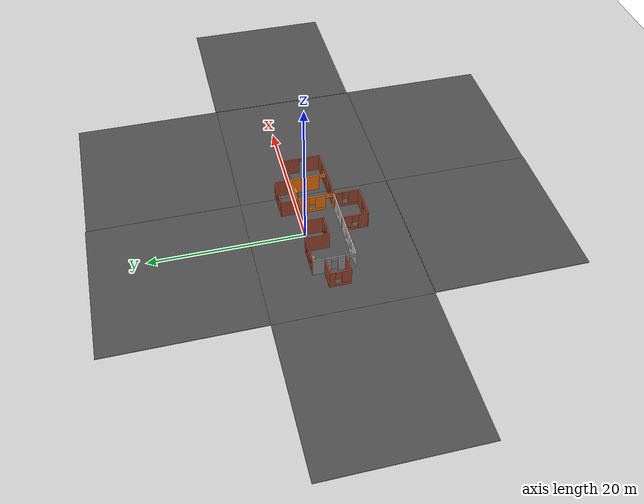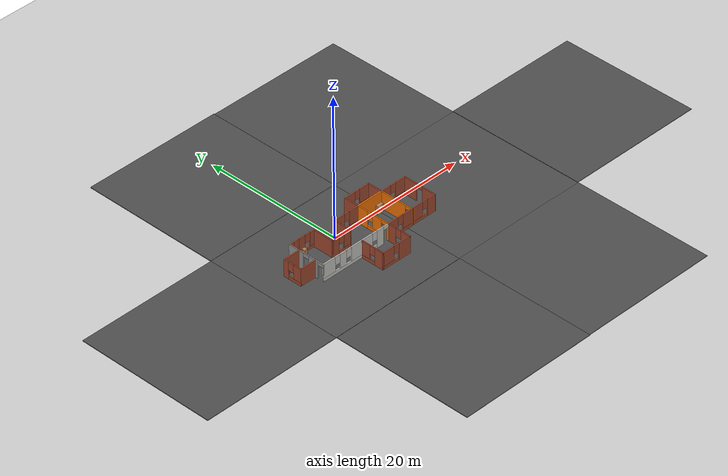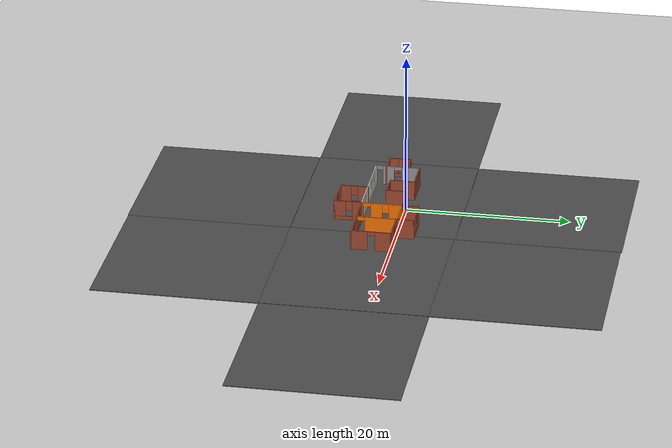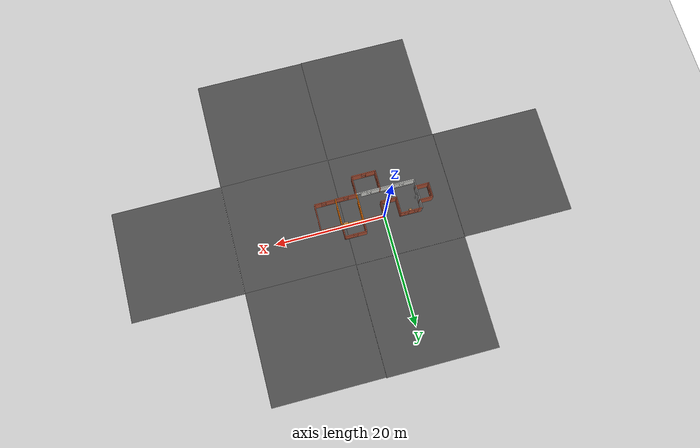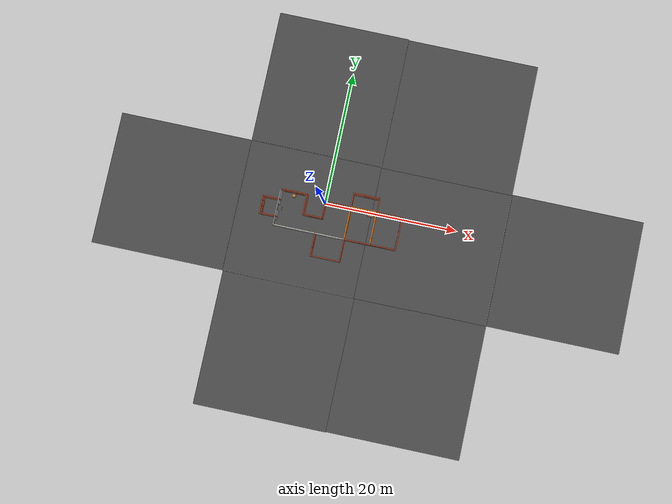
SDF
<sdf version="1.6">
 <world name="default">
  <plugin name="welcome" filename="libwelcome.so"/>
  <light name="sun" type="directional">
   <pose>0 0 10 0 -0 0</pose>
   <diffuse>0.8 0.8 0.8 1</diffuse>
   <specular>0.2 0.2 0.2 1</specular>
   <attenuation>
    <range>1000</range>
    <constant>0.9</constant>
    <linear>0.01</linear>
    <quadratic>0.001</quadratic>
   </attenuation>
   <direction>-0.5 0.1 -0.9</direction>
  </light>
  <model name="ground_plane">
   <static>1</static>
   <link name="link">
    <collision name="collision">
     <geometry><plane><normal>0 0 1</normal><size>100 100</size></plane></geometry>
     <surface>
      <contact><collide_bitmask>65535</collide_bitmask></contact>
      <friction><ode><mu>100</mu><mu2>50</mu2></ode></friction>
     </surface>
    </collision>
    <visual name="visual">
     <cast_shadows>0</cast_shadows>
     <geometry><plane><normal>0 0 1</normal><size>100 100</size></plane></geometry>
     <material>
      <script><uri>file://media/materials/scripts/gazebo.material</uri><name>Gazebo/Grey</name></script>
     </material>
    </visual>
   </link>
  </model>
  <gravity>0 0 -9.8</gravity>
  <magnetic_field>6e-06 2.3e-05 -4.2e-05</magnetic_field>
  <atmosphere type="adiabatic"/>
  <physics name="default_physics" default="0" type="ode">
   <max_step_size>0.001</max_step_size>
   <real_time_factor>1</real_time_factor>
   <real_time_update_rate>1000</real_time_update_rate>
  </physics>
  <scene><ambient>0.4 0.4 0.4 1</ambient><background>0.7 0.7 0.7 1</background><shadows>1</shadows></scene>
  <spherical_coordinates>
   <surface_model>EARTH_WGS84</surface_model>
   <latitude_deg>0</latitude_deg>
   <longitude_deg>0</longitude_deg>
   <elevation>0</elevation>
   <heading_deg>0</heading_deg>
  </spherical_coordinates>
  <model name="Level_1">
   <pose>1.32566 -2.96233 0 0 -0 0</pose>
   <link name="Door_3">
    <collision name="Door_3_Collision">
     <geometry><box><size>0.9 0.17 2</size></box></geometry>
     <pose>0 0 1 0 -0 0</pose>
    </collision>
    <visual name="Door_3_Visual">
     <pose>0 0 1 0 -0 0</pose>
     <geometry><box><size>0.9 0.17 2</size></box></geometry>
     <material>
      <script><uri>file://media/materials/scripts/gazebo.material</uri><name>Gazebo/Grey</name></script>
     </material>
    </visual>
    <pose>5.97774 3.20768 0 0 -0 0</pose>
   </link>
   <link name="Wall_0">
    <pose>-6.00277 3.55 0 0 -0 0</pose>
    <visual name="Wall_0_Visual_0">
     <pose>-1.66505 0 1.25 0 -0 0</pose>
     <geometry><box><size>0.669906 0.15 2.5</size></box></geometry>
     <material>
      <script><uri>file://media/materials/scripts/gazebo.material</uri><name>Gazebo/Bricks</name></script>
      <ambient>1 1 1 1</ambient>
     </material>
     <meta><layer>0</layer></meta>
    </visual>
    <collision name="Wall_0_Collision_0">
     <geometry><box><size>0.669906 0.15 2.5</size></box></geometry>
     <pose>-1.66505 0 1.25 0 -0 0</pose>
    </collision>
    <visual name="Wall_0_Visual_1">
     <pose>0.334953 0 0.25 0 -0 0</pose>
     <geometry><box><size>3.33009 0.15 0.5</size></box></geometry>
     <material>
      <script><uri>file://media/materials/scripts/gazebo.material</uri><name>Gazebo/Bricks</name></script>
      <ambient>1 1 1 1</ambient>
     </material>
     <meta><layer>0</layer></meta>
    </visual>
    <collision name="Wall_0_Collision_1">
     <geometry><box><size>3.33009 0.15 0.5</size></box></geometry>
     <pose>0.334953 0 0.25 0 -0 0</pose>
    </collision>
    <visual name="Wall_0_Visual_2">
     <pose>-0.050625 0 1.5 0 -0 0</pose>
     <geometry><box><size>0.958938 0.15 2</size></box></geometry>
     <material>
      <script><uri>file://media/materials/scripts/gazebo.material</uri><name>Gazebo/Bricks</name></script>
      <ambient>1 1 1 1</ambient>
     </material>
     <meta><layer>0</layer></meta>
    </visual>
    <collision name="Wall_0_Collision_2">
     <geometry><box><size>0.958938 0.15 2</size></box></geometry>
     <pose>-0.050625 0 1.5 0 -0 0</pose>
    </collision>
    <visual name="Wall_0_Visual_3">
     <pose>1.61442 0 1.5 0 -0 0</pose>
     <geometry><box><size>0.771156 0.15 2</size></box></geometry>
     <material>
      <script><uri>file://media/materials/scripts/gazebo.material</uri><name>Gazebo/Bricks</name></script>
      <ambient>1 1 1 1</ambient>
     </material>
     <meta><layer>0</layer></meta>
    </visual>
    <collision name="Wall_0_Collision_3">
     <geometry><box><size>0.771156 0.15 2</size></box></geometry>
     <pose>1.61442 0 1.5 0 -0 0</pose>
    </collision>
    <visual name="Wall_0_Visual_4">
     <pose>-0.930094 0 1.9 0 -0 0</pose>
     <geometry><box><size>0.8 0.15 1.2</size></box></geometry>
     <material>
      <script><uri>file://media/materials/scripts/gazebo.material</uri><name>Gazebo/Bricks</name></script>
      <ambient>1 1 1 1</ambient>
     </material>
     <meta><layer>0</layer></meta>
    </visual>
    <collision name="Wall_0_Collision_4">
     <geometry><box><size>0.8 0.15 1.2</size></box></geometry>
     <pose>-0.930094 0 1.9 0 -0 0</pose>
    </collision>
    <visual name="Wall_0_Visual_5">
     <pose>0.828844 0 1.9 0 -0 0</pose>
     <geometry><box><size>0.8 0.15 1.2</size></box></geometry>
     <material>
      <script><uri>file://media/materials/scripts/gazebo.material</uri><name>Gazebo/Bricks</name></script>
      <ambient>1 1 1 1</ambient>
     </material>
     <meta><layer>0</layer></meta>
    </visual>
    <collision name="Wall_0_Collision_5">
     <geometry><box><size>0.8 0.15 1.2</size></box></geometry>
     <pose>0.828844 0 1.9 0 -0 0</pose>
    </collision>
   </link>
   <link name="Wall_1">
    <collision name="Wall_1_Collision">
     <geometry><box><size>3.121 0.15 2.5</size></box></geometry>
     <pose>0 0 1.25 0 -0 0</pose>
    </collision>
    <visual name="Wall_1_Visual">
     <pose>0 0 1.25 0 -0 0</pose>
     <geometry><box><size>3.121 0.15 2.5</size></box></geometry>
     <material>
      <script><uri>file://media/materials/scripts/gazebo.material</uri><name>Gazebo/Bricks</name></script>
      <ambient>1 1 1 1</ambient>
     </material>
     <meta><layer>0</layer></meta>
    </visual>
    <pose>-4.07777 2.0645 0 0 0 -1.5708</pose>
   </link>
   <link name="Wall_10">
    <pose>-10.3228 0.751 0 0 0 -1.5708</pose>
    <visual name="Wall_10_Visual_0">
     <pose>-0.99483 0 1.25 0 -0 0</pose>
     <geometry><box><size>0.76034 0.15 2.5</size></box></geometry>
     <material>
      <script><uri>file://media/materials/scripts/gazebo.material</uri><name>Gazebo/Bricks</name></script>
      <ambient>1 1 1 1</ambient>
     </material>
     <meta><layer>0</layer></meta>
    </visual>
    <collision name="Wall_10_Collision_0">
     <geometry><box><size>0.76034 0.15 2.5</size></box></geometry>
     <pose>-0.99483 0 1.25 0 -0 0</pose>
    </collision>
    <visual name="Wall_10_Visual_1">
     <pose>0.38017 0 0.25 0 -0 0</pose>
     <geometry><box><size>1.98966 0.15 0.5</size></box></geometry>
     <material>
      <script><uri>file://media/materials/scripts/gazebo.material</uri><name>Gazebo/Bricks</name></script>
      <ambient>1 1 1 1</ambient>
     </material>
     <meta><layer>0</layer></meta>
    </visual>
    <collision name="Wall_10_Collision_1">
     <geometry><box><size>1.98966 0.15 0.5</size></box></geometry>
     <pose>0.38017 0 0.25 0 -0 0</pose>
    </collision>
    <visual name="Wall_10_Visual_2">
     <pose>0.78017 0 1.5 0 -0 0</pose>
     <geometry><box><size>1.18966 0.15 2</size></box></geometry>
     <material>
      <script><uri>file://media/materials/scripts/gazebo.material</uri><name>Gazebo/Bricks</name></script>
      <ambient>1 1 1 1</ambient>
     </material>
     <meta><layer>0</layer></meta>
    </visual>
    <collision name="Wall_10_Collision_2">
     <geometry><box><size>1.18966 0.15 2</size></box></geometry>
     <pose>0.78017 0 1.5 0 -0 0</pose>
    </collision>
    <visual name="Wall_10_Visual_3">
     <pose>-0.21466 0 1.9 0 -0 0</pose>
     <geometry><box><size>0.8 0.15 1.2</size></box></geometry>
     <material>
      <script><uri>file://media/materials/scripts/gazebo.material</uri><name>Gazebo/Bricks</name></script>
      <ambient>1 1 1 1</ambient>
     </material>
     <meta><layer>0</layer></meta>
    </visual>
    <collision name="Wall_10_Collision_3">
     <geometry><box><size>0.8 0.15 1.2</size></box></geometry>
     <pose>-0.21466 0 1.9 0 -0 0</pose>
    </collision>
   </link>
   <link name="Wall_11">
    <collision name="Wall_11_Collision">
     <geometry><box><size>2.5 0.15 2.5</size></box></geometry>
     <pose>0 0 1.25 0 -0 0</pose>
    </collision>
    <visual name="Wall_11_Visual">
     <pose>0 0 1.25 0 -0 0</pose>
     <geometry><box><size>2.5 0.15 2.5</size></box></geometry>
     <material>
      <script><uri>file://media/materials/scripts/gazebo.material</uri><name>Gazebo/Bricks</name></script>
      <ambient>1 1 1 1</ambient>
     </material>
     <meta><layer>0</layer></meta>
    </visual>
    <pose>-9.14777 -0.549 0 0 -0 0</pose>
   </link>
   <link name="Wall_13">
    <pose>4.54723 -1.8 0 0 -0 0</pose>
    <visual name="Wall_13_Visual_0">
     <pose>-1.18832 0 1.25 0 -0 0</pose>
     <geometry><box><size>1.62336 0.15 2.5</size></box></geometry>
     <material>
      <script><uri>file://media/materials/scripts/gazebo.material</uri><name>Gazebo/Bricks</name></script>
      <ambient>1 1 1 1</ambient>
     </material>
     <meta><layer>0</layer></meta>
    </visual>
    <collision name="Wall_13_Collision_0">
     <geometry><box><size>1.62336 0.15 2.5</size></box></geometry>
     <pose>-1.18832 0 1.25 0 -0 0</pose>
    </collision>
    <visual name="Wall_13_Visual_1">
     <pose>0.811681 0 0.25 0 -0 0</pose>
     <geometry><box><size>2.37664 0.15 0.5</size></box></geometry>
     <material>
      <script><uri>file://media/materials/scripts/gazebo.material</uri><name>Gazebo/Bricks</name></script>
      <ambient>1 1 1 1</ambient>
     </material>
     <meta><layer>0</layer></meta>
    </visual>
    <collision name="Wall_13_Collision_1">
     <geometry><box><size>2.37664 0.15 0.5</size></box></geometry>
     <pose>0.811681 0 0.25 0 -0 0</pose>
    </collision>
    <visual name="Wall_13_Visual_2">
     <pose>1.21168 0 1.5 0 -0 0</pose>
     <geometry><box><size>1.57664 0.15 2</size></box></geometry>
     <material>
      <script><uri>file://media/materials/scripts/gazebo.material</uri><name>Gazebo/Bricks</name></script>
      <ambient>1 1 1 1</ambient>
     </material>
     <meta><layer>0</layer></meta>
    </visual>
    <collision name="Wall_13_Collision_2">
     <geometry><box><size>1.57664 0.15 2</size></box></geometry>
     <pose>1.21168 0 1.5 0 -0 0</pose>
    </collision>
    <visual name="Wall_13_Visual_3">
     <pose>0.023361 0 1.9 0 -0 0</pose>
     <geometry><box><size>0.8 0.15 1.2</size></box></geometry>
     <material>
      <script><uri>file://media/materials/scripts/gazebo.material</uri><name>Gazebo/Bricks</name></script>
      <ambient>1 1 1 1</ambient>
     </material>
     <meta><layer>0</layer></meta>
    </visual>
    <collision name="Wall_13_Collision_3">
     <geometry><box><size>0.8 0.15 1.2</size></box></geometry>
     <pose>0.023361 0 1.9 0 -0 0</pose>
    </collision>
   </link>
   <link name="Wall_14">
    <pose>6.47223 0.625 0 0 -0 1.5708</pose>
    <visual name="Wall_14_Visual_0">
     <pose>-2.39992 0 1.25 0 -0 0</pose>
     <geometry><box><size>0.200158 0.15 2.5</size></box></geometry>
     <material>
      <script><uri>file://media/materials/scripts/gazebo.material</uri><name>Gazebo/Grey</name></script>
      <ambient>0.996078 0.47451 0.0196078 1</ambient>
     </material>
     <meta><layer>0</layer></meta>
    </visual>
    <collision name="Wall_14_Collision_0">
     <geometry><box><size>0.200158 0.15 2.5</size></box></geometry>
     <pose>-2.39992 0 1.25 0 -0 0</pose>
    </collision>
    <visual name="Wall_14_Visual_1">
     <pose>0.550079 0 1.25 0 -0 0</pose>
     <geometry><box><size>3.89984 0.15 2.5</size></box></geometry>
     <material>
      <script><uri>file://media/materials/scripts/gazebo.material</uri><name>Gazebo/Grey</name></script>
      <ambient>0.996078 0.47451 0.0196078 1</ambient>
     </material>
     <meta><layer>0</layer></meta>
    </visual>
    <collision name="Wall_14_Collision_1">
     <geometry><box><size>3.89984 0.15 2.5</size></box></geometry>
     <pose>0.550079 0 1.25 0 -0 0</pose>
    </collision>
    <visual name="Wall_14_Visual_2">
     <pose>-1.84984 0 2.25 0 -0 0</pose>
     <geometry><box><size>0.9 0.15 0.5</size></box></geometry>
     <material>
      <script><uri>file://media/materials/scripts/gazebo.material</uri><name>Gazebo/Grey</name></script>
      <ambient>0.996078 0.47451 0.0196078 1</ambient>
     </material>
     <meta><layer>0</layer></meta>
    </visual>
    <collision name="Wall_14_Collision_2">
     <geometry><box><size>0.9 0.15 0.5</size></box></geometry>
     <pose>-1.84984 0 2.25 0 -0 0</pose>
    </collision>
   </link>
   <link name="Wall_15">
    <collision name="Wall_15_Collision">
     <geometry><box><size>4 0.15 2.5</size></box></geometry>
     <pose>0 0 1.25 0 -0 0</pose>
    </collision>
    <visual name="Wall_15_Visual">
     <pose>0 0 1.25 0 -0 0</pose>
     <geometry><box><size>4 0.15 2.5</size></box></geometry>
     <material>
      <script><uri>file://media/materials/scripts/gazebo.material</uri><name>Gazebo/Grey</name></script>
      <ambient>0.996078 0.47451 0.0196078 1</ambient>
     </material>
     <meta><layer>0</layer></meta>
    </visual>
    <pose>4.54723 3.05 0 0 -0 3.14159</pose>
   </link>
   <link name="Wall_16">
    <collision name="Wall_16_Collision">
     <geometry><box><size>2.25 0.15 2.5</size></box></geometry>
     <pose>0 0 1.25 0 -0 0</pose>
    </collision>
    <visual name="Wall_16_Visual">
     <pose>0 0 1.25 0 -0 0</pose>
     <geometry><box><size>2.25 0.15 2.5</size></box></geometry>
     <material>
      <script><uri>file://media/materials/scripts/gazebo.material</uri><name>Gazebo/Bricks</name></script>
      <ambient>1 1 1 1</ambient>
     </material>
     <meta><layer>0</layer></meta>
    </visual>
    <pose>2.62223 4.1 0 0 -0 1.5708</pose>
   </link>
   <link name="Wall_17">
    <pose>4.54723 5.15 0 0 -0 0</pose>
    <visual name="Wall_17_Visual_0">
     <pose>-1.18832 0 1.25 0 -0 0</pose>
     <geometry><box><size>1.62336 0.15 2.5</size></box></geometry>
     <material>
      <script><uri>file://media/materials/scripts/gazebo.material</uri><name>Gazebo/Bricks</name></script>
      <ambient>1 1 1 1</ambient>
     </material>
     <meta><layer>0</layer></meta>
    </visual>
    <collision name="Wall_17_Collision_0">
     <geometry><box><size>1.62336 0.15 2.5</size></box></geometry>
     <pose>-1.18832 0 1.25 0 -0 0</pose>
    </collision>
    <visual name="Wall_17_Visual_1">
     <pose>0.811681 0 0.25 0 -0 0</pose>
     <geometry><box><size>2.37664 0.15 0.5</size></box></geometry>
     <material>
      <script><uri>file://media/materials/scripts/gazebo.material</uri><name>Gazebo/Bricks</name></script>
      <ambient>1 1 1 1</ambient>
     </material>
     <meta><layer>0</layer></meta>
    </visual>
    <collision name="Wall_17_Collision_1">
     <geometry><box><size>2.37664 0.15 0.5</size></box></geometry>
     <pose>0.811681 0 0.25 0 -0 0</pose>
    </collision>
    <visual name="Wall_17_Visual_2">
     <pose>1.21168 0 1.5 0 -0 0</pose>
     <geometry><box><size>1.57664 0.15 2</size></box></geometry>
     <material>
      <script><uri>file://media/materials/scripts/gazebo.material</uri><name>Gazebo/Bricks</name></script>
      <ambient>1 1 1 1</ambient>
     </material>
     <meta><layer>0</layer></meta>
    </visual>
    <collision name="Wall_17_Collision_2">
     <geometry><box><size>1.57664 0.15 2</size></box></geometry>
     <pose>1.21168 0 1.5 0 -0 0</pose>
    </collision>
    <visual name="Wall_17_Visual_3">
     <pose>0.023361 0 1.9 0 -0 0</pose>
     <geometry><box><size>0.8 0.15 1.2</size></box></geometry>
     <material>
      <script><uri>file://media/materials/scripts/gazebo.material</uri><name>Gazebo/Bricks</name></script>
      <ambient>1 1 1 1</ambient>
     </material>
     <meta><layer>0</layer></meta>
    </visual>
    <collision name="Wall_17_Collision_3">
     <geometry><box><size>0.8 0.15 1.2</size></box></geometry>
     <pose>0.023361 0 1.9 0 -0 0</pose>
    </collision>
   </link>
   <link name="Wall_18">
    <collision name="Wall_18_Collision">
     <geometry><box><size>2.25 0.15 2.5</size></box></geometry>
     <pose>0 0 1.25 0 -0 0</pose>
    </collision>
    <visual name="Wall_18_Visual">
     <pose>0 0 1.25 0 -0 0</pose>
     <geometry><box><size>2.25 0.15 2.5</size></box></geometry>
     <material>
      <script><uri>file://media/materials/scripts/gazebo.material</uri><name>Gazebo/Bricks</name></script>
      <ambient>1 1 1 1</ambient>
     </material>
     <meta><layer>0</layer></meta>
    </visual>
    <pose>6.47223 4.1 0 0 0 -1.5708</pose>
   </link>
   <link name="Wall_2">
    <pose>-2.65277 0.579 0 0 -0 0</pose>
    <visual name="Wall_2_Visual_0">
     <pose>-0.961732 0 1.25 0 -0 0</pose>
     <geometry><box><size>1.07654 0.15 2.5</size></box></geometry>
     <material>
      <script><uri>file://media/materials/scripts/gazebo.material</uri><name>Gazebo/Bricks</name></script>
      <ambient>1 1 1 1</ambient>
     </material>
     <meta><layer>0</layer></meta>
    </visual>
    <collision name="Wall_2_Collision_0">
     <geometry><box><size>1.07654 0.15 2.5</size></box></geometry>
     <pose>-0.961732 0 1.25 0 -0 0</pose>
    </collision>
    <visual name="Wall_2_Visual_1">
     <pose>0.538268 0 0.25 0 -0 0</pose>
     <geometry><box><size>1.92346 0.15 0.5</size></box></geometry>
     <material>
      <script><uri>file://media/materials/scripts/gazebo.material</uri><name>Gazebo/Bricks</name></script>
      <ambient>1 1 1 1</ambient>
     </material>
     <meta><layer>0</layer></meta>
    </visual>
    <collision name="Wall_2_Collision_1">
     <geometry><box><size>1.92346 0.15 0.5</size></box></geometry>
     <pose>0.538268 0 0.25 0 -0 0</pose>
    </collision>
    <visual name="Wall_2_Visual_2">
     <pose>0.938268 0 1.5 0 -0 0</pose>
     <geometry><box><size>1.12346 0.15 2</size></box></geometry>
     <material>
      <script><uri>file://media/materials/scripts/gazebo.material</uri><name>Gazebo/Bricks</name></script>
      <ambient>1 1 1 1</ambient>
     </material>
     <meta><layer>0</layer></meta>
    </visual>
    <collision name="Wall_2_Collision_2">
     <geometry><box><size>1.12346 0.15 2</size></box></geometry>
     <pose>0.938268 0 1.5 0 -0 0</pose>
    </collision>
    <visual name="Wall_2_Visual_3">
     <pose>-0.023464 0 1.9 0 -0 0</pose>
     <geometry><box><size>0.8 0.15 1.2</size></box></geometry>
     <material>
      <script><uri>file://media/materials/scripts/gazebo.material</uri><name>Gazebo/Bricks</name></script>
      <ambient>1 1 1 1</ambient>
     </material>
     <meta><layer>0</layer></meta>
    </visual>
    <collision name="Wall_2_Collision_3">
     <geometry><box><size>0.8 0.15 1.2</size></box></geometry>
     <pose>-0.023464 0 1.9 0 -0 0</pose>
    </collision>
   </link>
   <link name="Wall_20">
    <pose>2.62223 -3.475 0 0 0 -1.5708</pose>
    <visual name="Wall_20_Visual_0">
     <pose>-1.12713 0 1.25 0 -0 0</pose>
     <geometry><box><size>1.24575 0.15 2.5</size></box></geometry>
     <material>
      <script><uri>file://media/materials/scripts/gazebo.material</uri><name>Gazebo/Bricks</name></script>
      <ambient>1 1 1 1</ambient>
     </material>
     <meta><layer>0</layer></meta>
    </visual>
    <collision name="Wall_20_Collision_0">
     <geometry><box><size>1.24575 0.15 2.5</size></box></geometry>
     <pose>-1.12713 0 1.25 0 -0 0</pose>
    </collision>
    <visual name="Wall_20_Visual_1">
     <pose>0.622873 0 0.25 0 -0 0</pose>
     <geometry><box><size>2.25425 0.15 0.5</size></box></geometry>
     <material>
      <script><uri>file://media/materials/scripts/gazebo.material</uri><name>Gazebo/Bricks</name></script>
      <ambient>1 1 1 1</ambient>
     </material>
     <meta><layer>0</layer></meta>
    </visual>
    <collision name="Wall_20_Collision_1">
     <geometry><box><size>2.25425 0.15 0.5</size></box></geometry>
     <pose>0.622873 0 0.25 0 -0 0</pose>
    </collision>
    <visual name="Wall_20_Visual_2">
     <pose>1.02287 0 1.5 0 -0 0</pose>
     <geometry><box><size>1.45425 0.15 2</size></box></geometry>
     <material>
      <script><uri>file://media/materials/scripts/gazebo.material</uri><name>Gazebo/Bricks</name></script>
      <ambient>1 1 1 1</ambient>
     </material>
     <meta><layer>0</layer></meta>
    </visual>
    <collision name="Wall_20_Collision_2">
     <geometry><box><size>1.45425 0.15 2</size></box></geometry>
     <pose>1.02287 0 1.5 0 -0 0</pose>
    </collision>
    <visual name="Wall_20_Visual_3">
     <pose>-0.104254 0 1.9 0 -0 0</pose>
     <geometry><box><size>0.8 0.15 1.2</size></box></geometry>
     <material>
      <script><uri>file://media/materials/scripts/gazebo.material</uri><name>Gazebo/Bricks</name></script>
      <ambient>1 1 1 1</ambient>
     </material>
     <meta><layer>0</layer></meta>
    </visual>
    <collision name="Wall_20_Collision_3">
     <geometry><box><size>0.8 0.15 1.2</size></box></geometry>
     <pose>-0.104254 0 1.9 0 -0 0</pose>
    </collision>
   </link>
   <link name="Wall_21">
    <pose>0.447228 -5.15 0 0 -0 3.14159</pose>
    <visual name="Wall_21_Visual_0">
     <pose>-1.31113 0 1.25 0 -0 0</pose>
     <geometry><box><size>1.87773 0.15 2.5</size></box></geometry>
     <material>
      <script><uri>file://media/materials/scripts/gazebo.material</uri><name>Gazebo/Bricks</name></script>
      <ambient>1 1 1 1</ambient>
     </material>
     <meta><layer>0</layer></meta>
    </visual>
    <collision name="Wall_21_Collision_0">
     <geometry><box><size>1.87773 0.15 2.5</size></box></geometry>
     <pose>-1.31113 0 1.25 0 -0 0</pose>
    </collision>
    <visual name="Wall_21_Visual_1">
     <pose>0.938867 0 0.25 0 -0 0</pose>
     <geometry><box><size>2.62227 0.15 0.5</size></box></geometry>
     <material>
      <script><uri>file://media/materials/scripts/gazebo.material</uri><name>Gazebo/Bricks</name></script>
      <ambient>1 1 1 1</ambient>
     </material>
     <meta><layer>0</layer></meta>
    </visual>
    <collision name="Wall_21_Collision_1">
     <geometry><box><size>2.62227 0.15 0.5</size></box></geometry>
     <pose>0.938867 0 0.25 0 -0 0</pose>
    </collision>
    <visual name="Wall_21_Visual_2">
     <pose>1.33887 0 1.5 0 -0 0</pose>
     <geometry><box><size>1.82227 0.15 2</size></box></geometry>
     <material>
      <script><uri>file://media/materials/scripts/gazebo.material</uri><name>Gazebo/Bricks</name></script>
      <ambient>1 1 1 1</ambient>
     </material>
     <meta><layer>0</layer></meta>
    </visual>
    <collision name="Wall_21_Collision_2">
     <geometry><box><size>1.82227 0.15 2</size></box></geometry>
     <pose>1.33887 0 1.5 0 -0 0</pose>
    </collision>
    <visual name="Wall_21_Visual_3">
     <pose>0.027733 0 1.9 0 -0 0</pose>
     <geometry><box><size>0.8 0.15 1.2</size></box></geometry>
     <material>
      <script><uri>file://media/materials/scripts/gazebo.material</uri><name>Gazebo/Bricks</name></script>
      <ambient>1 1 1 1</ambient>
     </material>
     <meta><layer>0</layer></meta>
    </visual>
    <collision name="Wall_21_Collision_3">
     <geometry><box><size>0.8 0.15 1.2</size></box></geometry>
     <pose>0.027733 0 1.9 0 -0 0</pose>
    </collision>
   </link>
   <link name="Wall_22">
    <pose>-1.72777 -3.475 0 0 -0 1.5708</pose>
    <visual name="Wall_22_Visual_0">
     <pose>-1.07564 0 1.25 0 -0 0</pose>
     <geometry><box><size>1.34872 0.15 2.5</size></box></geometry>
     <material>
      <script><uri>file://media/materials/scripts/gazebo.material</uri><name>Gazebo/Bricks</name></script>
      <ambient>1 1 1 1</ambient>
     </material>
     <meta><layer>0</layer></meta>
    </visual>
    <collision name="Wall_22_Collision_0">
     <geometry><box><size>1.34872 0.15 2.5</size></box></geometry>
     <pose>-1.07564 0 1.25 0 -0 0</pose>
    </collision>
    <visual name="Wall_22_Visual_1">
     <pose>0.674359 0 0.25 0 -0 0</pose>
     <geometry><box><size>2.15128 0.15 0.5</size></box></geometry>
     <material>
      <script><uri>file://media/materials/scripts/gazebo.material</uri><name>Gazebo/Bricks</name></script>
      <ambient>1 1 1 1</ambient>
     </material>
     <meta><layer>0</layer></meta>
    </visual>
    <collision name="Wall_22_Collision_1">
     <geometry><box><size>2.15128 0.15 0.5</size></box></geometry>
     <pose>0.674359 0 0.25 0 -0 0</pose>
    </collision>
    <visual name="Wall_22_Visual_2">
     <pose>1.07436 0 1.5 0 -0 0</pose>
     <geometry><box><size>1.35128 0.15 2</size></box></geometry>
     <material>
      <script><uri>file://media/materials/scripts/gazebo.material</uri><name>Gazebo/Bricks</name></script>
      <ambient>1 1 1 1</ambient>
     </material>
     <meta><layer>0</layer></meta>
    </visual>
    <collision name="Wall_22_Collision_2">
     <geometry><box><size>1.35128 0.15 2</size></box></geometry>
     <pose>1.07436 0 1.5 0 -0 0</pose>
    </collision>
    <visual name="Wall_22_Visual_3">
     <pose>-0.001282 0 1.9 0 -0 0</pose>
     <geometry><box><size>0.8 0.15 1.2</size></box></geometry>
     <material>
      <script><uri>file://media/materials/scripts/gazebo.material</uri><name>Gazebo/Bricks</name></script>
      <ambient>1 1 1 1</ambient>
     </material>
     <meta><layer>0</layer></meta>
    </visual>
    <collision name="Wall_22_Collision_3">
     <geometry><box><size>0.8 0.15 1.2</size></box></geometry>
     <pose>-0.001282 0 1.9 0 -0 0</pose>
    </collision>
   </link>
   <link name="Wall_24">
    <pose>8.39723 3.05 0 0 -0 0</pose>
    <visual name="Wall_24_Visual_0">
     <pose>-1.23126 0 1.25 0 -0 0</pose>
     <geometry><box><size>1.53749 0.15 2.5</size></box></geometry>
     <material>
      <script><uri>file://media/materials/scripts/gazebo.material</uri><name>Gazebo/Bricks</name></script>
      <ambient>1 1 1 1</ambient>
     </material>
     <meta><layer>0</layer></meta>
    </visual>
    <collision name="Wall_24_Collision_0">
     <geometry><box><size>1.53749 0.15 2.5</size></box></geometry>
     <pose>-1.23126 0 1.25 0 -0 0</pose>
    </collision>
    <visual name="Wall_24_Visual_1">
     <pose>0.768744 0 0.25 0 -0 0</pose>
     <geometry><box><size>2.46251 0.15 0.5</size></box></geometry>
     <material>
      <script><uri>file://media/materials/scripts/gazebo.material</uri><name>Gazebo/Bricks</name></script>
      <ambient>1 1 1 1</ambient>
     </material>
     <meta><layer>0</layer></meta>
    </visual>
    <collision name="Wall_24_Collision_1">
     <geometry><box><size>2.46251 0.15 0.5</size></box></geometry>
     <pose>0.768744 0 0.25 0 -0 0</pose>
    </collision>
    <visual name="Wall_24_Visual_2">
     <pose>1.16874 0 1.5 0 -0 0</pose>
     <geometry><box><size>1.66251 0.15 2</size></box></geometry>
     <material>
      <script><uri>file://media/materials/scripts/gazebo.material</uri><name>Gazebo/Bricks</name></script>
      <ambient>1 1 1 1</ambient>
     </material>
     <meta><layer>0</layer></meta>
    </visual>
    <collision name="Wall_24_Collision_2">
     <geometry><box><size>1.66251 0.15 2</size></box></geometry>
     <pose>1.16874 0 1.5 0 -0 0</pose>
    </collision>
    <visual name="Wall_24_Visual_3">
     <pose>-0.062511 0 1.9 0 -0 0</pose>
     <geometry><box><size>0.8 0.15 1.2</size></box></geometry>
     <material>
      <script><uri>file://media/materials/scripts/gazebo.material</uri><name>Gazebo/Bricks</name></script>
      <ambient>1 1 1 1</ambient>
     </material>
     <meta><layer>0</layer></meta>
    </visual>
    <collision name="Wall_24_Collision_3">
     <geometry><box><size>0.8 0.15 1.2</size></box></geometry>
     <pose>-0.062511 0 1.9 0 -0 0</pose>
    </collision>
   </link>
   <link name="Wall_25">
    <pose>10.3047 0.6445 0 0 0 -1.57807</pose>
    <visual name="Wall_25_Visual_0">
     <pose>-1.46301 0 1.25 0 -0 0</pose>
     <geometry><box><size>2.03517 0.15 2.5</size></box></geometry>
     <material>
      <script><uri>file://media/materials/scripts/gazebo.material</uri><name>Gazebo/Bricks</name></script>
      <ambient>1 1 1 1</ambient>
     </material>
     <meta><layer>0</layer></meta>
    </visual>
    <collision name="Wall_25_Collision_0">
     <geometry><box><size>2.03517 0.15 2.5</size></box></geometry>
     <pose>-1.46301 0 1.25 0 -0 0</pose>
    </collision>
    <visual name="Wall_25_Visual_1">
     <pose>1.46759 0 1.25 0 -0 0</pose>
     <geometry><box><size>2.02603 0.15 2.5</size></box></geometry>
     <material>
      <script><uri>file://media/materials/scripts/gazebo.material</uri><name>Gazebo/Bricks</name></script>
      <ambient>1 1 1 1</ambient>
     </material>
     <meta><layer>0</layer></meta>
    </visual>
    <collision name="Wall_25_Collision_1">
     <geometry><box><size>2.02603 0.15 2.5</size></box></geometry>
     <pose>1.46759 0 1.25 0 -0 0</pose>
    </collision>
    <visual name="Wall_25_Visual_2">
     <pose>0.004573 0 2.25 0 -0 0</pose>
     <geometry><box><size>0.9 0.15 0.5</size></box></geometry>
     <material>
      <script><uri>file://media/materials/scripts/gazebo.material</uri><name>Gazebo/Bricks</name></script>
      <ambient>1 1 1 1</ambient>
     </material>
     <meta><layer>0</layer></meta>
    </visual>
    <collision name="Wall_25_Collision_2">
     <geometry><box><size>0.9 0.15 0.5</size></box></geometry>
     <pose>0.004573 0 2.25 0 -0 0</pose>
    </collision>
   </link>
   <link name="Wall_26">
    <pose>8.48723 -1.761 0 0 -0 3.14159</pose>
    <visual name="Wall_26_Visual_0">
     <pose>-1.21964 0 1.25 0 -0 0</pose>
     <geometry><box><size>1.31072 0.15 2.5</size></box></geometry>
     <material>
      <script><uri>file://media/materials/scripts/gazebo.material</uri><name>Gazebo/Bricks</name></script>
      <ambient>1 1 1 1</ambient>
     </material>
     <meta><layer>0</layer></meta>
    </visual>
    <collision name="Wall_26_Collision_0">
     <geometry><box><size>1.31072 0.15 2.5</size></box></geometry>
     <pose>-1.21964 0 1.25 0 -0 0</pose>
    </collision>
    <visual name="Wall_26_Visual_1">
     <pose>0.655361 0 0.25 0 -0 0</pose>
     <geometry><box><size>2.43928 0.15 0.5</size></box></geometry>
     <material>
      <script><uri>file://media/materials/scripts/gazebo.material</uri><name>Gazebo/Bricks</name></script>
      <ambient>1 1 1 1</ambient>
     </material>
     <meta><layer>0</layer></meta>
    </visual>
    <collision name="Wall_26_Collision_1">
     <geometry><box><size>2.43928 0.15 0.5</size></box></geometry>
     <pose>0.655361 0 0.25 0 -0 0</pose>
    </collision>
    <visual name="Wall_26_Visual_2">
     <pose>1.05536 0 1.5 0 -0 0</pose>
     <geometry><box><size>1.63928 0.15 2</size></box></geometry>
     <material>
      <script><uri>file://media/materials/scripts/gazebo.material</uri><name>Gazebo/Bricks</name></script>
      <ambient>1 1 1 1</ambient>
     </material>
     <meta><layer>0</layer></meta>
    </visual>
    <collision name="Wall_26_Collision_2">
     <geometry><box><size>1.63928 0.15 2</size></box></geometry>
     <pose>1.05536 0 1.5 0 -0 0</pose>
    </collision>
    <visual name="Wall_26_Visual_3">
     <pose>-0.164277 0 1.9 0 -0 0</pose>
     <geometry><box><size>0.8 0.15 1.2</size></box></geometry>
     <material>
      <script><uri>file://media/materials/scripts/gazebo.material</uri><name>Gazebo/Bricks</name></script>
      <ambient>1 1 1 1</ambient>
     </material>
     <meta><layer>0</layer></meta>
    </visual>
    <collision name="Wall_26_Collision_3">
     <geometry><box><size>0.8 0.15 1.2</size></box></geometry>
     <pose>-0.164277 0 1.9 0 -0 0</pose>
    </collision>
   </link>
   <link name="Wall_3">
    <collision name="Wall_3_Collision">
     <geometry><box><size>2.621 0.15 2.5</size></box></geometry>
     <pose>0 0 1.25 0 -0 0</pose>
    </collision>
    <visual name="Wall_3_Visual">
     <pose>0 0 1.25 0 -0 0</pose>
     <geometry><box><size>2.621 0.15 2.5</size></box></geometry>
     <material>
      <script><uri>file://media/materials/scripts/gazebo.material</uri><name>Gazebo/Bricks</name></script>
      <ambient>1 1 1 1</ambient>
     </material>
     <meta><layer>0</layer></meta>
    </visual>
    <pose>-1.22777 1.8145 0 0 -0 1.5708</pose>
   </link>
   <link name="Wall_4">
    <pose>0.697228 3.05 0 0 -0 0</pose>
    <visual name="Wall_4_Visual_0">
     <pose>-1.18056 0 1.25 0 -0 0</pose>
     <geometry><box><size>1.63888 0.15 2.5</size></box></geometry>
     <material>
      <script><uri>file://media/materials/scripts/gazebo.material</uri><name>Gazebo/Bricks</name></script>
      <ambient>1 1 1 1</ambient>
     </material>
     <meta><layer>0</layer></meta>
    </visual>
    <collision name="Wall_4_Collision_0">
     <geometry><box><size>1.63888 0.15 2.5</size></box></geometry>
     <pose>-1.18056 0 1.25 0 -0 0</pose>
    </collision>
    <visual name="Wall_4_Visual_1">
     <pose>0.819438 0 0.25 0 -0 0</pose>
     <geometry><box><size>2.36112 0.15 0.5</size></box></geometry>
     <material>
      <script><uri>file://media/materials/scripts/gazebo.material</uri><name>Gazebo/Bricks</name></script>
      <ambient>1 1 1 1</ambient>
     </material>
     <meta><layer>0</layer></meta>
    </visual>
    <collision name="Wall_4_Collision_1">
     <geometry><box><size>2.36112 0.15 0.5</size></box></geometry>
     <pose>0.819438 0 0.25 0 -0 0</pose>
    </collision>
    <visual name="Wall_4_Visual_2">
     <pose>1.21944 0 1.5 0 -0 0</pose>
     <geometry><box><size>1.56112 0.15 2</size></box></geometry>
     <material>
      <script><uri>file://media/materials/scripts/gazebo.material</uri><name>Gazebo/Bricks</name></script>
      <ambient>1 1 1 1</ambient>
     </material>
     <meta><layer>0</layer></meta>
    </visual>
    <collision name="Wall_4_Collision_2">
     <geometry><box><size>1.56112 0.15 2</size></box></geometry>
     <pose>1.21944 0 1.5 0 -0 0</pose>
    </collision>
    <visual name="Wall_4_Visual_3">
     <pose>0.038876 0 1.9 0 -0 0</pose>
     <geometry><box><size>0.8 0.15 1.2</size></box></geometry>
     <material>
      <script><uri>file://media/materials/scripts/gazebo.material</uri><name>Gazebo/Bricks</name></script>
      <ambient>1 1 1 1</ambient>
     </material>
     <meta><layer>0</layer></meta>
    </visual>
    <collision name="Wall_4_Collision_3">
     <geometry><box><size>0.8 0.15 1.2</size></box></geometry>
     <pose>0.038876 0 1.9 0 -0 0</pose>
    </collision>
   </link>
   <link name="Wall_5">
    <pose>2.62223 0.625 0 0 0 -1.5708</pose>
    <visual name="Wall_5_Visual_0">
     <pose>-1.68598 0 1.25 0 -0 0</pose>
     <geometry><box><size>1.62804 0.15 2.5</size></box></geometry>
     <material>
      <script><uri>file://media/materials/scripts/gazebo.material</uri><name>Gazebo/Grey</name></script>
      <ambient>0.996078 0.47451 0.0196078 1</ambient>
     </material>
     <meta><layer>0</layer></meta>
    </visual>
    <collision name="Wall_5_Collision_0">
     <geometry><box><size>1.62804 0.15 2.5</size></box></geometry>
     <pose>-1.68598 0 1.25 0 -0 0</pose>
    </collision>
    <visual name="Wall_5_Visual_1">
     <pose>2.36474 0 1.25 0 -0 0</pose>
     <geometry><box><size>0.270516 0.15 2.5</size></box></geometry>
     <material>
      <script><uri>file://media/materials/scripts/gazebo.material</uri><name>Gazebo/Grey</name></script>
      <ambient>0.996078 0.47451 0.0196078 1</ambient>
     </material>
     <meta><layer>0</layer></meta>
    </visual>
    <collision name="Wall_5_Collision_1">
     <geometry><box><size>0.270516 0.15 2.5</size></box></geometry>
     <pose>2.36474 0 1.25 0 -0 0</pose>
    </collision>
    <visual name="Wall_5_Visual_2">
     <pose>0.228764 0 0.25 0 -0 0</pose>
     <geometry><box><size>2.20144 0.15 0.5</size></box></geometry>
     <material>
      <script><uri>file://media/materials/scripts/gazebo.material</uri><name>Gazebo/Grey</name></script>
      <ambient>0.996078 0.47451 0.0196078 1</ambient>
     </material>
     <meta><layer>0</layer></meta>
    </visual>
    <collision name="Wall_5_Collision_2">
     <geometry><box><size>2.20144 0.15 0.5</size></box></geometry>
     <pose>0.228764 0 0.25 0 -0 0</pose>
    </collision>
    <visual name="Wall_5_Visual_3">
     <pose>0.628764 0 1.5 0 -0 0</pose>
     <geometry><box><size>1.40144 0.15 2</size></box></geometry>
     <material>
      <script><uri>file://media/materials/scripts/gazebo.material</uri><name>Gazebo/Grey</name></script>
      <ambient>0.996078 0.47451 0.0196078 1</ambient>
     </material>
     <meta><layer>0</layer></meta>
    </visual>
    <collision name="Wall_5_Collision_3">
     <geometry><box><size>1.40144 0.15 2</size></box></geometry>
     <pose>0.628764 0 1.5 0 -0 0</pose>
    </collision>
    <visual name="Wall_5_Visual_4">
     <pose>-0.471957 0 1.9 0 -0 0</pose>
     <geometry><box><size>0.8 0.15 1.2</size></box></geometry>
     <material>
      <script><uri>file://media/materials/scripts/gazebo.material</uri><name>Gazebo/Grey</name></script>
      <ambient>0.996078 0.47451 0.0196078 1</ambient>
     </material>
     <meta><layer>0</layer></meta>
    </visual>
    <collision name="Wall_5_Collision_4">
     <geometry><box><size>0.8 0.15 1.2</size></box></geometry>
     <pose>-0.471957 0 1.9 0 -0 0</pose>
    </collision>
    <visual name="Wall_5_Visual_5">
     <pose>1.77948 0 2.25 0 -0 0</pose>
     <geometry><box><size>0.9 0.15 0.5</size></box></geometry>
     <material>
      <script><uri>file://media/materials/scripts/gazebo.material</uri><name>Gazebo/Grey</name></script>
      <ambient>0.996078 0.47451 0.0196078 1</ambient>
     </material>
     <meta><layer>0</layer></meta>
    </visual>
    <collision name="Wall_5_Collision_5">
     <geometry><box><size>0.9 0.15 0.5</size></box></geometry>
     <pose>1.77948 0 2.25 0 -0 0</pose>
    </collision>
   </link>
   <link name="Wall_6">
    <pose>-2.67777 -1.8 0 0 -0 3.14159</pose>
    <visual name="Wall_6_Visual_0">
     <pose>-5.3406 0 1.25 0 -0 0</pose>
     <geometry><box><size>0.068795 0.15 2.5</size></box></geometry>
     <material>
      <script><uri>file://media/materials/scripts/gazebo.material</uri><name>Gazebo/CeilingTiled</name></script>
      <ambient>1 1 1 1</ambient>
     </material>
     <meta><layer>0</layer></meta>
    </visual>
    <collision name="Wall_6_Collision_0">
     <geometry><box><size>0.068795 0.15 2.5</size></box></geometry>
     <pose>-5.3406 0 1.25 0 -0 0</pose>
    </collision>
    <visual name="Wall_6_Visual_1">
     <pose>-3.89897 0 1.25 0 -0 0</pose>
     <geometry><box><size>1.01447 0.15 2.5</size></box></geometry>
     <material>
      <script><uri>file://media/materials/scripts/gazebo.material</uri><name>Gazebo/CeilingTiled</name></script>
      <ambient>1 1 1 1</ambient>
     </material>
     <meta><layer>0</layer></meta>
    </visual>
    <collision name="Wall_6_Collision_1">
     <geometry><box><size>1.01447 0.15 2.5</size></box></geometry>
     <pose>-3.89897 0 1.25 0 -0 0</pose>
    </collision>
    <visual name="Wall_6_Visual_2">
     <pose>0.991635 0 0.25 0 -0 0</pose>
     <geometry><box><size>8.76673 0.15 0.5</size></box></geometry>
     <material>
      <script><uri>file://media/materials/scripts/gazebo.material</uri><name>Gazebo/CeilingTiled</name></script>
      <ambient>1 1 1 1</ambient>
     </material>
     <meta><layer>0</layer></meta>
    </visual>
    <collision name="Wall_6_Collision_2">
     <geometry><box><size>8.76673 0.15 0.5</size></box></geometry>
     <pose>0.991635 0 0.25 0 -0 0</pose>
    </collision>
    <visual name="Wall_6_Visual_3">
     <pose>-0.881005 0 1.5 0 -0 0</pose>
     <geometry><box><size>3.42145 0.15 2</size></box></geometry>
     <material>
      <script><uri>file://media/materials/scripts/gazebo.material</uri><name>Gazebo/CeilingTiled</name></script>
      <ambient>1 1 1 1</ambient>
     </material>
     <meta><layer>0</layer></meta>
    </visual>
    <collision name="Wall_6_Collision_3">
     <geometry><box><size>3.42145 0.15 2</size></box></geometry>
     <pose>-0.881005 0 1.5 0 -0 0</pose>
    </collision>
    <visual name="Wall_6_Visual_4">
     <pose>2.12678 0 1.5 0 -0 0</pose>
     <geometry><box><size>0.994117 0.15 2</size></box></geometry>
     <material>
      <script><uri>file://media/materials/scripts/gazebo.material</uri><name>Gazebo/CeilingTiled</name></script>
      <ambient>1 1 1 1</ambient>
     </material>
     <meta><layer>0</layer></meta>
    </visual>
    <collision name="Wall_6_Collision_4">
     <geometry><box><size>0.994117 0.15 2</size></box></geometry>
     <pose>2.12678 0 1.5 0 -0 0</pose>
    </collision>
    <visual name="Wall_6_Visual_5">
     <pose>4.39942 0 1.5 0 -0 0</pose>
     <geometry><box><size>1.95116 0.15 2</size></box></geometry>
     <material>
      <script><uri>file://media/materials/scripts/gazebo.material</uri><name>Gazebo/CeilingTiled</name></script>
      <ambient>1 1 1 1</ambient>
     </material>
     <meta><layer>0</layer></meta>
    </visual>
    <collision name="Wall_6_Collision_5">
     <geometry><box><size>1.95116 0.15 2</size></box></geometry>
     <pose>4.39942 0 1.5 0 -0 0</pose>
    </collision>
    <visual name="Wall_6_Visual_6">
     <pose>-2.99173 0 1.9 0 -0 0</pose>
     <geometry><box><size>0.8 0.15 1.2</size></box></geometry>
     <material>
      <script><uri>file://media/materials/scripts/gazebo.material</uri><name>Gazebo/CeilingTiled</name></script>
      <ambient>1 1 1 1</ambient>
     </material>
     <meta><layer>0</layer></meta>
    </visual>
    <collision name="Wall_6_Collision_6">
     <geometry><box><size>0.8 0.15 1.2</size></box></geometry>
     <pose>-2.99173 0 1.9 0 -0 0</pose>
    </collision>
    <visual name="Wall_6_Visual_7">
     <pose>1.22972 0 1.9 0 -0 0</pose>
     <geometry><box><size>0.8 0.15 1.2</size></box></geometry>
     <material>
      <script><uri>file://media/materials/scripts/gazebo.material</uri><name>Gazebo/CeilingTiled</name></script>
      <ambient>1 1 1 1</ambient>
     </material>
     <meta><layer>0</layer></meta>
    </visual>
    <collision name="Wall_6_Collision_7">
     <geometry><box><size>0.8 0.15 1.2</size></box></geometry>
     <pose>1.22972 0 1.9 0 -0 0</pose>
    </collision>
    <visual name="Wall_6_Visual_8">
     <pose>3.02384 0 1.9 0 -0 0</pose>
     <geometry><box><size>0.8 0.15 1.2</size></box></geometry>
     <material>
      <script><uri>file://media/materials/scripts/gazebo.material</uri><name>Gazebo/CeilingTiled</name></script>
      <ambient>1 1 1 1</ambient>
     </material>
     <meta><layer>0</layer></meta>
    </visual>
    <collision name="Wall_6_Collision_8">
     <geometry><box><size>0.8 0.15 1.2</size></box></geometry>
     <pose>3.02384 0 1.9 0 -0 0</pose>
    </collision>
    <visual name="Wall_6_Visual_9">
     <pose>-4.85621 0 2.25 0 -0 0</pose>
     <geometry><box><size>0.9 0.15 0.5</size></box></geometry>
     <material>
      <script><uri>file://media/materials/scripts/gazebo.material</uri><name>Gazebo/CeilingTiled</name></script>
      <ambient>1 1 1 1</ambient>
     </material>
     <meta><layer>0</layer></meta>
    </visual>
    <collision name="Wall_6_Collision_9">
     <geometry><box><size>0.9 0.15 0.5</size></box></geometry>
     <pose>-4.85621 0 2.25 0 -0 0</pose>
    </collision>
   </link>
   <link name="Wall_7">
    <pose>-7.97777 0.875 0 0 -0 1.5708</pose>
    <visual name="Wall_7_Visual_0">
     <pose>-2.74745 0 1.25 0 -0 0</pose>
     <geometry><box><size>0.005101 0.15 2.5</size></box></geometry>
     <material>
      <script><uri>file://media/materials/scripts/gazebo.material</uri><name>Gazebo/Grey</name></script>
      <ambient>1 1 1 1</ambient>
     </material>
     <meta><layer>0</layer></meta>
    </visual>
    <collision name="Wall_7_Collision_0">
     <geometry><box><size>0.005101 0.15 2.5</size></box></geometry>
     <pose>-2.74745 0 1.25 0 -0 0</pose>
    </collision>
    <visual name="Wall_7_Visual_1">
     <pose>-1.14201 0 1.25 0 -0 0</pose>
     <geometry><box><size>1.40578 0.15 2.5</size></box></geometry>
     <material>
      <script><uri>file://media/materials/scripts/gazebo.material</uri><name>Gazebo/Grey</name></script>
      <ambient>1 1 1 1</ambient>
     </material>
     <meta><layer>0</layer></meta>
    </visual>
    <collision name="Wall_7_Collision_1">
     <geometry><box><size>1.40578 0.15 2.5</size></box></geometry>
     <pose>-1.14201 0 1.25 0 -0 0</pose>
    </collision>
    <visual name="Wall_7_Visual_2">
     <pose>1.60544 0 1.25 0 -0 0</pose>
     <geometry><box><size>2.28912 0.15 2.5</size></box></geometry>
     <material>
      <script><uri>file://media/materials/scripts/gazebo.material</uri><name>Gazebo/Grey</name></script>
      <ambient>1 1 1 1</ambient>
     </material>
     <meta><layer>0</layer></meta>
    </visual>
    <collision name="Wall_7_Collision_2">
     <geometry><box><size>2.28912 0.15 2.5</size></box></geometry>
     <pose>1.60544 0 1.25 0 -0 0</pose>
    </collision>
    <visual name="Wall_7_Visual_3">
     <pose>-2.2949 0 2.25 0 -0 0</pose>
     <geometry><box><size>0.9 0.15 0.5</size></box></geometry>
     <material>
      <script><uri>file://media/materials/scripts/gazebo.material</uri><name>Gazebo/Grey</name></script>
      <ambient>1 1 1 1</ambient>
     </material>
     <meta><layer>0</layer></meta>
    </visual>
    <collision name="Wall_7_Collision_3">
     <geometry><box><size>0.9 0.15 0.5</size></box></geometry>
     <pose>-2.2949 0 2.25 0 -0 0</pose>
    </collision>
    <visual name="Wall_7_Visual_4">
     <pose>0.010884 0 2.25 0 -0 0</pose>
     <geometry><box><size>0.9 0.15 0.5</size></box></geometry>
     <material>
      <script><uri>file://media/materials/scripts/gazebo.material</uri><name>Gazebo/Grey</name></script>
      <ambient>1 1 1 1</ambient>
     </material>
     <meta><layer>0</layer></meta>
    </visual>
    <collision name="Wall_7_Collision_4">
     <geometry><box><size>0.9 0.15 0.5</size></box></geometry>
     <pose>0.010884 0 2.25 0 -0 0</pose>
    </collision>
   </link>
   <link name="Wall_9">
    <collision name="Wall_9_Collision">
     <geometry><box><size>2.5 0.15 2.5</size></box></geometry>
     <pose>0 0 1.25 0 -0 0</pose>
    </collision>
    <visual name="Wall_9_Visual">
     <pose>0 0 1.25 0 -0 0</pose>
     <geometry><box><size>2.5 0.15 2.5</size></box></geometry>
     <material>
      <script><uri>file://media/materials/scripts/gazebo.material</uri><name>Gazebo/Bricks</name></script>
      <ambient>1 1 1 1</ambient>
     </material>
     <meta><layer>0</layer></meta>
    </visual>
    <pose>-9.14777 2.051 0 0 -0 3.14159</pose>
   </link>
   <static>1</static>
  </model>
  <model name="bookshelf">
   <static>1</static>
   <link name="link">
    <inertial><mass>1</mass></inertial>
    <collision name="back">
     <pose>0 0.005 0.6 0 -0 0</pose>
     <geometry><box><size>0.9 0.01 1.2</size></box></geometry>
    </collision>
    <visual name="visual1">
     <pose>0 0.005 0.6 0 -0 0</pose>
     <geometry><box><size>0.9 0.01 1.2</size></box></geometry>
     <material>
      <script><uri>file://media/materials/scripts/gazebo.material</uri><name>Gazebo/Wood</name></script>
     </material>
    </visual>
    <collision name="left_side">
     <pose>0.45 -0.195 0.6 0 -0 0</pose>
     <geometry><box><size>0.02 0.4 1.2</size></box></geometry>
    </collision>
    <visual name="visual2">
     <pose>0.45 -0.195 0.6 0 -0 0</pose>
     <geometry><box><size>0.02 0.4 1.2</size></box></geometry>
     <material>
      <script><uri>file://media/materials/scripts/gazebo.material</uri><name>Gazebo/Wood</name></script>
     </material>
    </visual>
    <collision name="right_side">
     <pose>-0.45 -0.195 0.6 0 -0 0</pose>
     <geometry><box><size>0.02 0.4 1.2</size></box></geometry>
    </collision>
    <visual name="visual3">
     <pose>-0.45 -0.195 0.6 0 -0 0</pose>
     <geometry><box><size>0.02 0.4 1.2</size></box></geometry>
     <material>
      <script><uri>file://media/materials/scripts/gazebo.material</uri><name>Gazebo/Wood</name></script>
     </material>
    </visual>
    <collision name="bottom">
     <pose>0 -0.195 0.03 0 -0 0</pose>
     <geometry><box><size>0.88 0.4 0.06</size></box></geometry>
    </collision>
    <visual name="visual4">
     <pose>0 -0.195 0.03 0 -0 0</pose>
     <geometry><box><size>0.88 0.4 0.06</size></box></geometry>
     <material>
      <script><uri>file://media/materials/scripts/gazebo.material</uri><name>Gazebo/Wood</name></script>
     </material>
    </visual>
    <collision name="top">
     <pose>0 -0.195 1.19 0 -0 0</pose>
     <geometry><box><size>0.88 0.4 0.02</size></box></geometry>
    </collision>
    <visual name="visual5">
     <pose>0 -0.195 1.19 0 -0 0</pose>
     <geometry><box><size>0.88 0.4 0.02</size></box></geometry>
     <material>
      <script><uri>file://media/materials/scripts/gazebo.material</uri><name>Gazebo/Wood</name></script>
     </material>
    </visual>
    <collision name="low_shelf">
     <pose>0 -0.195 0.43 0 -0 0</pose>
     <geometry><box><size>0.88 0.4 0.02</size></box></geometry>
    </collision>
    <visual name="visual6">
     <pose>0 -0.195 0.43 0 -0 0</pose>
     <geometry><box><size>0.88 0.4 0.02</size></box></geometry>
     <material>
      <script><uri>file://media/materials/scripts/gazebo.material</uri><name>Gazebo/Wood</name></script>
     </material>
    </visual>
    <collision name="high_shelf">
     <pose>0 -0.195 0.8 0 -0 0</pose>
     <geometry><box><size>0.88 0.4 0.02</size></box></geometry>
    </collision>
    <visual name="visual7">
     <pose>0 -0.195 0.8 0 -0 0</pose>
     <geometry><box><size>0.88 0.4 0.02</size></box></geometry>
     <material>
      <script><uri>file://media/materials/scripts/gazebo.material</uri><name>Gazebo/Wood</name></script>
     </material>
    </visual>
   </link>
   <pose>7.01962 -0.178814 0 0 -0 0</pose>
  </model>
  <model name="cabinet">
   <static>1</static>
   <link name="cabinet_bottom_plate">
    <inertial>
     <pose>0 0 -1 0 -0 0</pose>
     <inertia><ixx>2.05</ixx><ixy>0</ixy><ixz>0</ixz><iyy>2.05</iyy><iyz>0</iyz><izz>2.05</izz></inertia>
     <mass>25</mass>
    </inertial>
    <collision name="cabinet_bottom_plate_geom">
     <pose>0 0 0.01 0 -0 0</pose>
     <geometry><box><size>0.45 0.45 0.02</size></box></geometry>
    </collision>
    <visual name="cabinet_bottom_plate_geom_visual">
     <pose>0 0 0.01 0 -0 0</pose>
     <geometry><box><size>0.45 0.45 0.02</size></box></geometry>
     <material>
      <script><uri>file://media/materials/scripts/gazebo.material</uri><name>Gazebo/Wood</name></script>
     </material>
    </visual>
    <collision name="cabinet_bottom_plate_geom_cabinet_back_plate">
     <pose>0.235 0 0.51 0 -0 0</pose>
     <geometry><box><size>0.02 0.45 1.02</size></box></geometry>
    </collision>
    <visual name="cabinet_bottom_plate_geom_cabinet_back_plate_visual">
     <pose>0.235 0 0.51 0 -0 0</pose>
     <geometry><box><size>0.02 0.45 1.02</size></box></geometry>
     <material>
      <script><uri>file://media/materials/scripts/gazebo.material</uri><name>Gazebo/Wood</name></script>
     </material>
    </visual>
    <collision name="cabinet_bottom_plate_geom_cabinet_left_plate">
     <pose>0 0.235 0.51 0 -0 0</pose>
     <geometry><box><size>0.45 0.02 1.02</size></box></geometry>
    </collision>
    <visual name="cabinet_bottom_plate_geom_cabinet_left_plate_visual">
     <pose>0 0.235 0.51 0 -0 0</pose>
     <geometry><box><size>0.45 0.02 1.02</size></box></geometry>
     <material>
      <script><uri>file://media/materials/scripts/gazebo.material</uri><name>Gazebo/Wood</name></script>
     </material>
    </visual>
    <collision name="cabinet_bottom_plate_geom_cabinet_middle_plate">
     <pose>0 0 0.51 0 -0 0</pose>
     <geometry><box><size>0.45 0.45 0.02</size></box></geometry>
    </collision>
    <visual name="cabinet_bottom_plate_geom_cabinet_middle_plate_visual">
     <pose>0 0 0.51 0 -0 0</pose>
     <geometry><box><size>0.45 0.45 0.02</size></box></geometry>
     <material>
      <script><uri>file://media/materials/scripts/gazebo.material</uri><name>Gazebo/Wood</name></script>
     </material>
    </visual>
    <collision name="cabinet_bottom_plate_geom_cabinet_right_plate">
     <pose>0 -0.235 0.51 0 -0 0</pose>
     <geometry><box><size>0.45 0.02 1.02</size></box></geometry>
    </collision>
    <visual name="cabinet_bottom_plate_geom_cabinet_right_plate_visual">
     <pose>0 -0.235 0.51 0 -0 0</pose>
     <geometry><box><size>0.45 0.02 1.02</size></box></geometry>
     <material>
      <script><uri>file://media/materials/scripts/gazebo.material</uri><name>Gazebo/Wood</name></script>
     </material>
    </visual>
    <collision name="cabinet_bottom_plate_geom_cabinet_top_plate">
     <pose>0 0 1.01 0 -0 0</pose>
     <geometry><box><size>0.45 0.45 0.02</size></box></geometry>
    </collision>
    <visual name="cabinet_bottom_plate_geom_cabinet_top_plate_visual">
     <pose>0 0 1.01 0 -0 0</pose>
     <geometry><box><size>0.45 0.45 0.02</size></box></geometry>
     <material>
      <script><uri>file://media/materials/scripts/gazebo.material</uri><name>Gazebo/Wood</name></script>
     </material>
    </visual>
   </link>
   <pose>-4.74516 0.130822 0 0 -0 0</pose>
  </model>
  <model name="asphalt_plane">
   <static>1</static>
   <link name="link">
    <collision name="collision"><geometry><box><size>20 20 0.1</size></box></geometry></collision>
    <visual name="visual">
     <cast_shadows>0</cast_shadows>
     <geometry><box><size>20 20 0.1</size></box></geometry>
     <material>
      <script>
       <uri>model://asphalt_plane/materials/scripts</uri>
       <uri>model://asphalt_plane/materials/textures</uri>
       <name>vrc/asphalt</name>
      </script>
     </material>
    </visual>
   </link>
   <pose>-2.87285 -2.90879 0 0 -0 0</pose>
  </model>
  <model name="asphalt_plane_0">
   <static>1</static>
   <link name="link">
    <collision name="collision"><geometry><box><size>20 20 0.1</size></box></geometry></collision>
    <visual name="visual">
     <cast_shadows>0</cast_shadows>
     <geometry><box><size>20 20 0.1</size></box></geometry>
     <material>
      <script>
       <uri>model://asphalt_plane/materials/scripts</uri>
       <uri>model://asphalt_plane/materials/textures</uri>
       <name>vrc/asphalt</name>
      </script>
     </material>
    </visual>
   </link>
   <pose>17.1247 -2.96156 0 0 -0 0</pose>
  </model>
  <model name="Robots_clone">
   <link name="link_0">
    <pose>0 0 0.19 0 -0 0</pose>
    <inertial>
     <mass>1</mass>
     <inertia>
      <ixx>0.166667</ixx>
      <ixy>0</ixy>
      <ixz>0</ixz>
      <iyy>0.166667</iyy>
      <iyz>0</iyz>
      <izz>0.166667</izz>
     </inertia>
    </inertial>
    <visual name="visual">
     <geometry><box><size>0.2 0.4 0.1</size></box></geometry>
     <material>
      <lighting>1</lighting>
      <script><uri>file://media/materials/scripts/gazebo.material</uri><name>Gazebo/Grey</name></script>
      <shader type="pixel"><normal_map>__default__</normal_map></shader>
      <ambient>0.3 0.3 0.3 1</ambient>
      <diffuse>0.7 0.7 0.7 1</diffuse>
      <specular>0.01 0.01 0.01 1</specular>
      <emissive>0 0 0 1</emissive>
     </material>
    </visual>
    <collision name="collision">
     <geometry><box><size>0.2 0.4 0.1</size></box></geometry>
     <surface>
      <friction>
       <ode><mu>1</mu><mu2>1</mu2><fdir1>0 0 0</fdir1><slip1>0</slip1><slip2>0</slip2></ode>
       <torsional>
        <coefficient>1</coefficient>
        <patch_radius>0</patch_radius>
        <surface_radius>0</surface_radius>
        <use_patch_radius>1</use_patch_radius>
        <ode><slip>0</slip></ode>
       </torsional>
      </friction>
      <bounce><restitution_coefficient>0</restitution_coefficient><threshold>1e+06</threshold></bounce>
      <contact>
       <collide_without_contact>0</collide_without_contact>
       <collide_without_contact_bitmask>1</collide_without_contact_bitmask>
       <collide_bitmask>1</collide_bitmask>
       <ode>
        <soft_cfm>0</soft_cfm>
        <soft_erp>0.2</soft_erp>
        <kp>1e+13</kp>
        <kd>1</kd>
        <max_vel>0.01</max_vel>
        <min_depth>0</min_depth>
       </ode>
       <bullet>
        <split_impulse>1</split_impulse>
        <split_impulse_penetration_threshold>-0.01</split_impulse_penetration_threshold>
        <soft_cfm>0</soft_cfm>
        <soft_erp>0.2</soft_erp>
        <kp>1e+13</kp>
        <kd>1</kd>
       </bullet>
      </contact>
     </surface>
    </collision>
   </link>
   <link name="link_0_0">
    <pose>0 -0.2 0.2 1.5707 -0 0</pose>
    <inertial>
     <mass>1</mass>
     <inertia><ixx>0.145833</ixx><ixy>0</ixy><ixz>0</ixz><iyy>0.145833</iyy><iyz>0</iyz><izz>0.125</izz></inertia>
    </inertial>
    <visual name="visual">
     <geometry><cylinder><radius>0.1</radius><length>0.1</length></cylinder></geometry>
     <material>
      <lighting>1</lighting>
      <script><uri>file://media/materials/scripts/gazebo.material</uri><name>Gazebo/Grey</name></script>
      <shader type="pixel"><normal_map>__default__</normal_map></shader>
      <ambient>0.3 0.3 0.3 1</ambient>
      <diffuse>0.7 0.7 0.7 1</diffuse>
      <specular>0.01 0.01 0.01 1</specular>
      <emissive>0 0 0 1</emissive>
     </material>
    </visual>
    <collision name="collision">
     <geometry><cylinder><radius>0.1</radius><length>0.1</length></cylinder></geometry>
     <surface>
      <friction>
       <ode><mu>1</mu><mu2>1</mu2><fdir1>0 0 0</fdir1><slip1>0</slip1><slip2>0</slip2></ode>
       <torsional>
        <coefficient>1</coefficient>
        <patch_radius>0</patch_radius>
        <surface_radius>0</surface_radius>
        <use_patch_radius>1</use_patch_radius>
        <ode><slip>0</slip></ode>
       </torsional>
      </friction>
      <bounce><restitution_coefficient>0</restitution_coefficient><threshold>1e+06</threshold></bounce>
      <contact>
       <collide_without_contact>0</collide_without_contact>
       <collide_without_contact_bitmask>1</collide_without_contact_bitmask>
       <collide_bitmask>1</collide_bitmask>
       <ode>
        <soft_cfm>0</soft_cfm>
        <soft_erp>0.2</soft_erp>
        <kp>1e+13</kp>
        <kd>1</kd>
        <max_vel>0.01</max_vel>
        <min_depth>0</min_depth>
       </ode>
       <bullet>
        <split_impulse>1</split_impulse>
        <split_impulse_penetration_threshold>-0.01</split_impulse_penetration_threshold>
        <soft_cfm>0</soft_cfm>
        <soft_erp>0.2</soft_erp>
        <kp>1e+13</kp>
        <kd>1</kd>
       </bullet>
      </contact>
     </surface>
    </collision>
   </link>
   <link name="link_0_0_clone">
    <pose>-0 0.2 0.2 1.5707 -0 0</pose>
    <inertial>
     <mass>1</mass>
     <inertia><ixx>0.145833</ixx><ixy>0</ixy><ixz>0</ixz><iyy>0.145833</iyy><iyz>0</iyz><izz>0.125</izz></inertia>
    </inertial>
    <visual name="visual_0">
     <geometry><cylinder><radius>0.1</radius><length>0.1</length></cylinder></geometry>
     <material>
      <lighting>1</lighting>
      <script><uri>file://media/materials/scripts/gazebo.material</uri><name>Gazebo/Grey</name></script>
      <shader type="pixel"><normal_map>__default__</normal_map></shader>
      <ambient>0.3 0.3 0.3 1</ambient>
      <diffuse>0.7 0.7 0.7 1</diffuse>
      <specular>0.01 0.01 0.01 1</specular>
      <emissive>0 0 0 1</emissive>
     </material>
    </visual>
    <collision name="collision">
     <geometry><cylinder><radius>0.1</radius><length>0.1</length></cylinder></geometry>
     <surface>
      <friction>
       <ode><mu>1</mu><mu2>1</mu2><fdir1>0 0 0</fdir1><slip1>0</slip1><slip2>0</slip2></ode>
       <torsional>
        <coefficient>1</coefficient>
        <patch_radius>0</patch_radius>
        <surface_radius>0</surface_radius>
        <use_patch_radius>1</use_patch_radius>
        <ode><slip>0</slip></ode>
       </torsional>
      </friction>
      <bounce><restitution_coefficient>0</restitution_coefficient><threshold>1e+06</threshold></bounce>
      <contact>
       <collide_without_contact>0</collide_without_contact>
       <collide_without_contact_bitmask>1</collide_without_contact_bitmask>
       <collide_bitmask>1</collide_bitmask>
       <ode>
        <soft_cfm>0</soft_cfm>
        <soft_erp>0.2</soft_erp>
        <kp>1e+13</kp>
        <kd>1</kd>
        <max_vel>0.01</max_vel>
        <min_depth>0</min_depth>
       </ode>
       <bullet>
        <split_impulse>1</split_impulse>
        <split_impulse_penetration_threshold>-0.01</split_impulse_penetration_threshold>
        <soft_cfm>0</soft_cfm>
        <soft_erp>0.2</soft_erp>
        <kp>1e+13</kp>
        <kd>1</kd>
       </bullet>
      </contact>
     </surface>
    </collision>
   </link>
   <link name="link_0_1">
    <pose>-0 -0 0.3 0 6e-06 0.000162</pose>
    <inertial>
     <mass>1</mass>
     <inertia><ixx>0.1</ixx><ixy>0</ixy><ixz>0</ixz><iyy>0.1</iyy><iyz>0</iyz><izz>0.1</izz></inertia>
    </inertial>
    <visual name="visual">
     <geometry><sphere><radius>0.05</radius></sphere></geometry>
     <material>
      <lighting>1</lighting>
      <script><uri>file://media/materials/scripts/gazebo.material</uri><name>Gazebo/Grey</name></script>
      <shader type="pixel"><normal_map>__default__</normal_map></shader>
      <ambient>0.3 0.3 0.3 1</ambient>
      <diffuse>0.7 0.7 0.7 1</diffuse>
      <specular>0.01 0.01 0.01 1</specular>
      <emissive>0 0 0 1</emissive>
     </material>
    </visual>
    <collision name="collision">
     <geometry><sphere><radius>0.05</radius></sphere></geometry>
     <surface>
      <friction>
       <ode><mu>1</mu><mu2>1</mu2><fdir1>0 0 0</fdir1><slip1>0</slip1><slip2>0</slip2></ode>
       <torsional>
        <coefficient>1</coefficient>
        <patch_radius>0</patch_radius>
        <surface_radius>0</surface_radius>
        <use_patch_radius>1</use_patch_radius>
        <ode><slip>0</slip></ode>
       </torsional>
      </friction>
      <bounce><restitution_coefficient>0</restitution_coefficient><threshold>1e+06</threshold></bounce>
      <contact>
       <collide_without_contact>0</collide_without_contact>
       <collide_without_contact_bitmask>1</collide_without_contact_bitmask>
       <collide_bitmask>1</collide_bitmask>
       <ode>
        <soft_cfm>0</soft_cfm>
        <soft_erp>0.2</soft_erp>
        <kp>1e+13</kp>
        <kd>1</kd>
        <max_vel>0.01</max_vel>
        <min_depth>0</min_depth>
       </ode>
       <bullet>
        <split_impulse>1</split_impulse>
        <split_impulse_penetration_threshold>-0.01</split_impulse_penetration_threshold>
        <soft_cfm>0</soft_cfm>
        <soft_erp>0.2</soft_erp>
        <kp>1e+13</kp>
        <kd>1</kd>
       </bullet>
      </contact>
     </surface>
    </collision>
   </link>
   <joint name="link_0_JOINT_0" type="revolute">
    <parent>link_0</parent>
    <child>link_0_0</child>
    <axis>
     <xyz>0 0 1</xyz>
     <use_parent_model_frame>0</use_parent_model_frame>
     <limit>
      <lower>-1.79769e+308</lower>
      <upper>1.79769e+308</upper>
      <effort>-1</effort>
      <velocity>-1</velocity>
     </limit>
     <dynamics>
      <spring_reference>0</spring_reference>
      <spring_stiffness>0</spring_stiffness>
      <damping>0</damping>
      <friction>0</friction>
     </dynamics>
    </axis>
    <physics>
     <ode><limit><cfm>0</cfm><erp>0.2</erp></limit><suspension><cfm>0</cfm><erp>0.2</erp></suspension></ode>
    </physics>
   </joint>
   <joint name="link_0_JOINT_1_0" type="ball">
    <parent>link_0</parent>
    <child>link_0_1</child>
    <physics>
     <ode><limit><cfm>0</cfm><erp>0.2</erp></limit><suspension><cfm>0</cfm><erp>0.2</erp></suspension></ode>
    </physics>
   </joint>
   <joint name="link_0_JOINT_1" type="revolute">
    <parent>link_0</parent>
    <child>link_0_0_clone</child>
    <axis>
     <xyz>0 0 1</xyz>
     <use_parent_model_frame>0</use_parent_model_frame>
     <limit>
      <lower>-1.79769e+308</lower>
      <upper>1.79769e+308</upper>
      <effort>-1</effort>
      <velocity>-1</velocity>
     </limit>
     <dynamics>
      <spring_reference>0</spring_reference>
      <spring_stiffness>0</spring_stiffness>
      <damping>0</damping>
      <friction>0</friction>
     </dynamics>
    </axis>
    <physics>
     <ode><limit><cfm>0</cfm><erp>0.2</erp></limit><suspension><cfm>0</cfm><erp>0.2</erp></suspension></ode>
    </physics>
   </joint>
   <joint name="link_0_JOINT_2" type="revolute">
    <parent>link_0</parent>
    <child>link_0_0</child>
    <axis>
     <xyz>0 0 1</xyz>
     <use_parent_model_frame>0</use_parent_model_frame>
     <limit>
      <lower>-1.79769e+308</lower>
      <upper>1.79769e+308</upper>
      <effort>-1</effort>
      <velocity>-1</velocity>
     </limit>
     <dynamics>
      <spring_reference>0</spring_reference>
      <spring_stiffness>0</spring_stiffness>
      <damping>0</damping>
      <friction>0</friction>
     </dynamics>
    </axis>
    <physics>
     <ode><limit><cfm>0</cfm><erp>0.2</erp></limit><suspension><cfm>0</cfm><erp>0.2</erp></suspension></ode>
    </physics>
   </joint>
   <joint name="link_0_JOINT_3" type="revolute">
    <parent>link_0</parent>
    <child>link_0_0_clone</child>
    <axis>
     <xyz>0 0 1</xyz>
     <use_parent_model_frame>0</use_parent_model_frame>
     <limit>
      <lower>-1.79769e+308</lower>
      <upper>1.79769e+308</upper>
      <effort>-1</effort>
      <velocity>-1</velocity>
     </limit>
     <dynamics>
      <spring_reference>0</spring_reference>
      <spring_stiffness>0</spring_stiffness>
      <damping>0</damping>
      <friction>0</friction>
     </dynamics>
    </axis>
    <physics>
     <ode><limit><cfm>0</cfm><erp>0.2</erp></limit><suspension><cfm>0</cfm><erp>0.2</erp></suspension></ode>
    </physics>
   </joint>
   <static>0</static>
   <pose>-6.20894 -2.09402 -0.026462 -2e-06 -0.490014 -0.035232</pose>
  </model>
  <model name="asphalt_plane_1">
   <static>1</static>
   <link name="link">
    <collision name="collision"><geometry><box><size>20 20 0.1</size></box></geometry></collision>
    <visual name="visual">
     <cast_shadows>0</cast_shadows>
     <geometry><box><size>20 20 0.1</size></box></geometry>
     <material>
      <script>
       <uri>model://asphalt_plane/materials/scripts</uri>
       <uri>model://asphalt_plane/materials/textures</uri>
       <name>vrc/asphalt</name>
      </script>
     </material>
    </visual>
   </link>
   <pose>-2.85824 17.1298 0 0 -0 0</pose>
  </model>
  <model name="asphalt_plane_2">
   <static>1</static>
   <link name="link">
    <collision name="collision"><geometry><box><size>20 20 0.1</size></box></geometry></collision>
    <visual name="visual">
     <cast_shadows>0</cast_shadows>
     <geometry><box><size>20 20 0.1</size></box></geometry>
     <material>
      <script>
       <uri>model://asphalt_plane/materials/scripts</uri>
       <uri>model://asphalt_plane/materials/textures</uri>
       <name>vrc/asphalt</name>
      </script>
     </material>
    </visual>
   </link>
   <pose>17.1542 17.012 0 0 -0 0</pose>
  </model>
  <model name="asphalt_plane_3">
   <static>1</static>
   <link name="link">
    <collision name="collision"><geometry><box><size>20 20 0.1</size></box></geometry></collision>
    <visual name="visual">
     <cast_shadows>0</cast_shadows>
     <geometry><box><size>20 20 0.1</size></box></geometry>
     <material>
      <script>
       <uri>model://asphalt_plane/materials/scripts</uri>
       <uri>model://asphalt_plane/materials/textures</uri>
       <name>vrc/asphalt</name>
      </script>
     </material>
    </visual>
   </link>
   <pose>-22.8774 -2.90567 0 0 -0 0</pose>
  </model>
  <model name="asphalt_plane_4">
   <static>1</static>
   <link name="link">
    <collision name="collision"><geometry><box><size>20 20 0.1</size></box></geometry></collision>
    <visual name="visual">
     <cast_shadows>0</cast_shadows>
     <geometry><box><size>20 20 0.1</size></box></geometry>
     <material>
      <script>
       <uri>model://asphalt_plane/materials/scripts</uri>
       <uri>model://asphalt_plane/materials/textures</uri>
       <name>vrc/asphalt</name>
      </script>
     </material>
    </visual>
   </link>
   <pose>37.186 -2.87622 0 0 -0 0</pose>
  </model>
  <model name="asphalt_plane_5">
   <static>1</static>
   <link name="link">
    <collision name="collision"><geometry><box><size>20 20 0.1</size></box></geometry></collision>
    <visual name="visual">
     <cast_shadows>0</cast_shadows>
     <geometry><box><size>20 20 0.1</size></box></geometry>
     <material>
      <script>
       <uri>model://asphalt_plane/materials/scripts</uri>
       <uri>model://asphalt_plane/materials/textures</uri>
       <name>vrc/asphalt</name>
      </script>
     </material>
    </visual>
   </link>
   <pose>-2.77362 -22.9605 0 0 -0 0</pose>
  </model>
  <model name="asphalt_plane_6">
   <static>1</static>
   <link name="link">
    <collision name="collision"><geometry><box><size>20 20 0.1</size></box></geometry></collision>
    <visual name="visual">
     <cast_shadows>0</cast_shadows>
     <geometry><box><size>20 20 0.1</size></box></geometry>
     <material>
      <script>
       <uri>model://asphalt_plane/materials/scripts</uri>
       <uri>model://asphalt_plane/materials/textures</uri>
       <name>vrc/asphalt</name>
      </script>
     </material>
    </visual>
   </link>
   <pose>17.1827 -22.8912 0 0 -0 0</pose>
  </model>
 </world>
</sdf>
